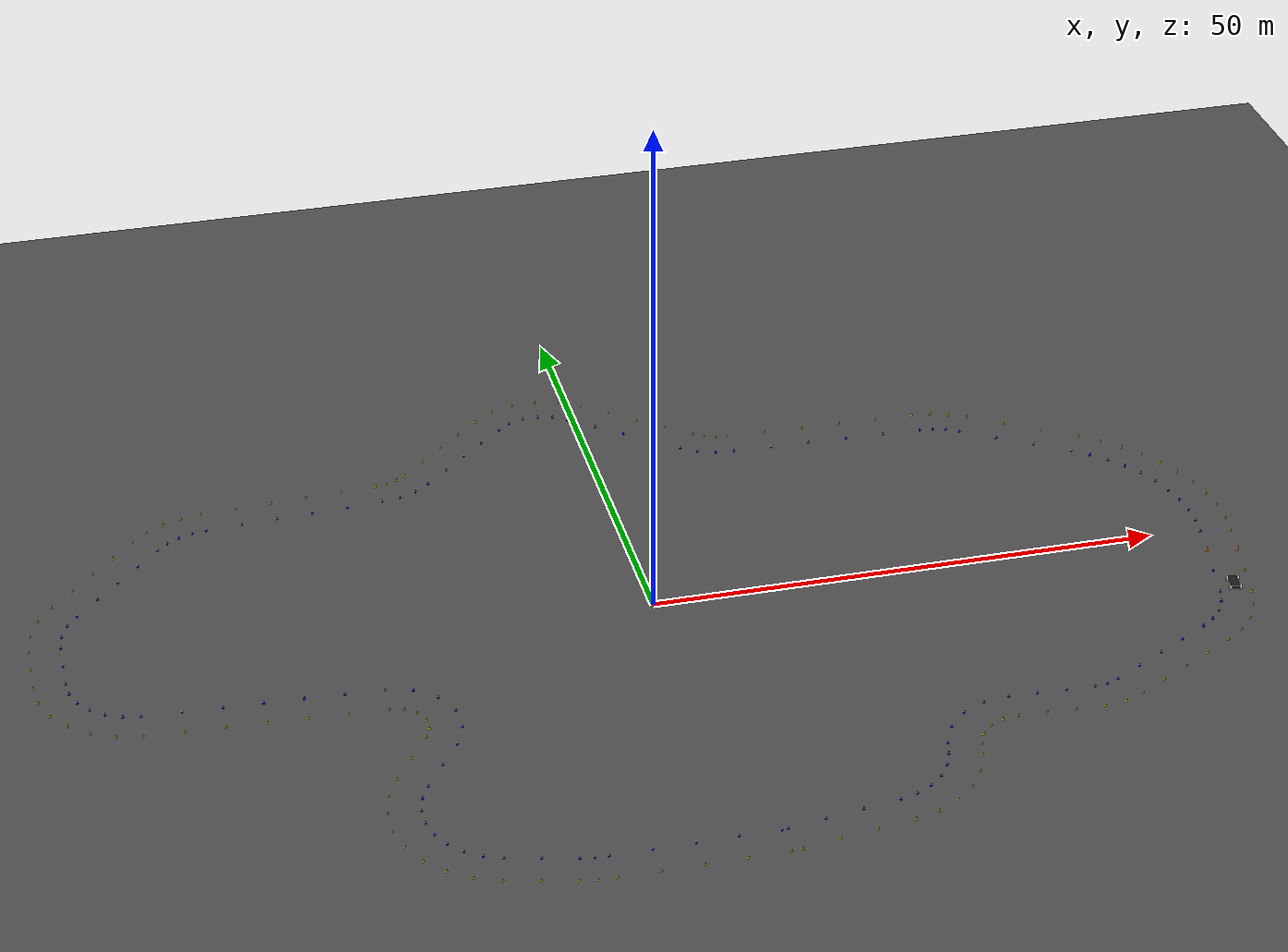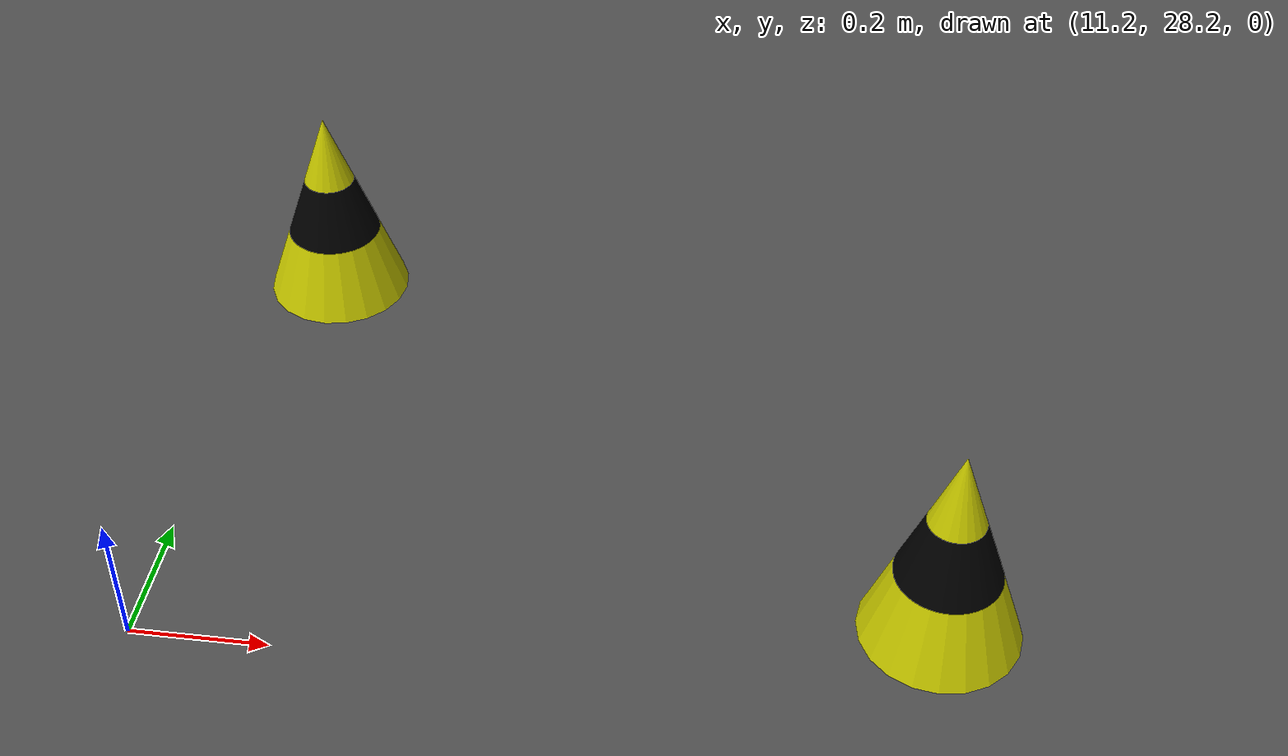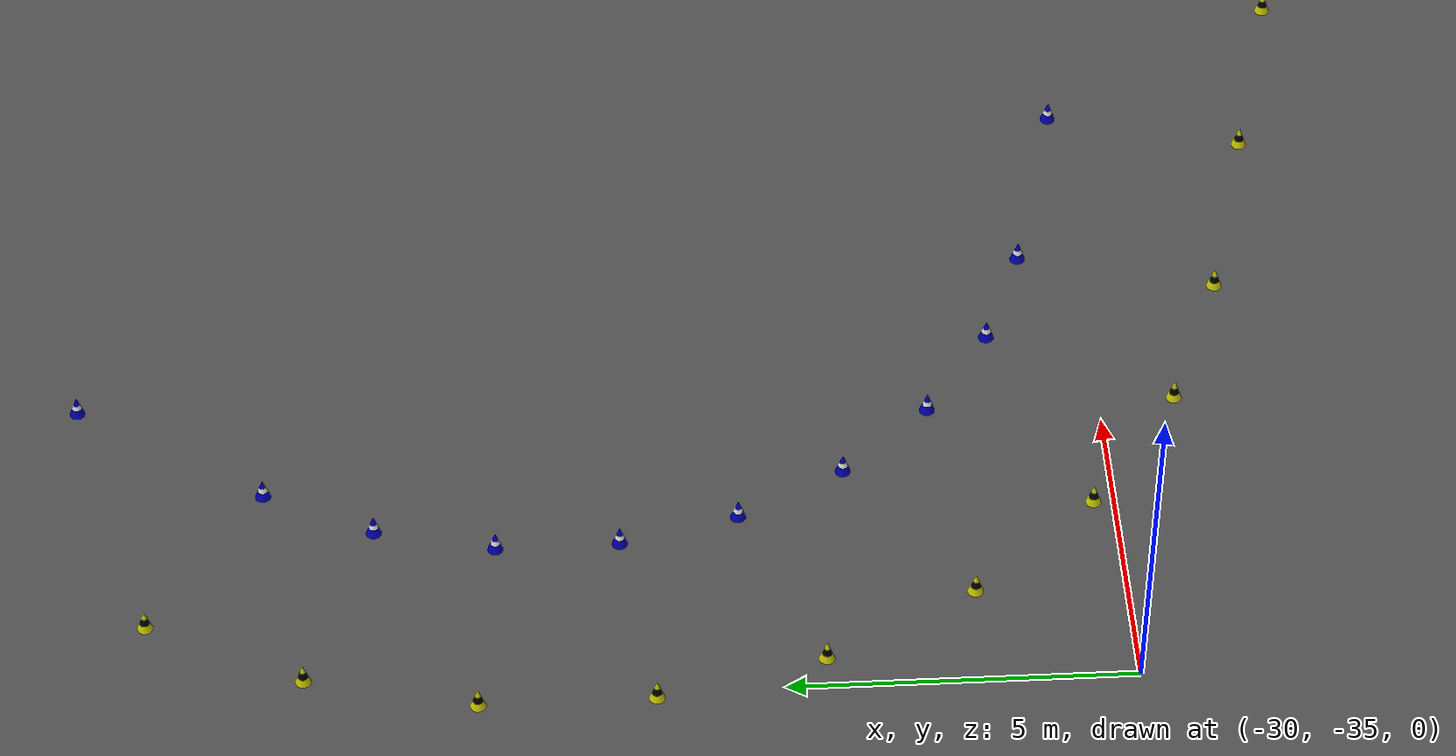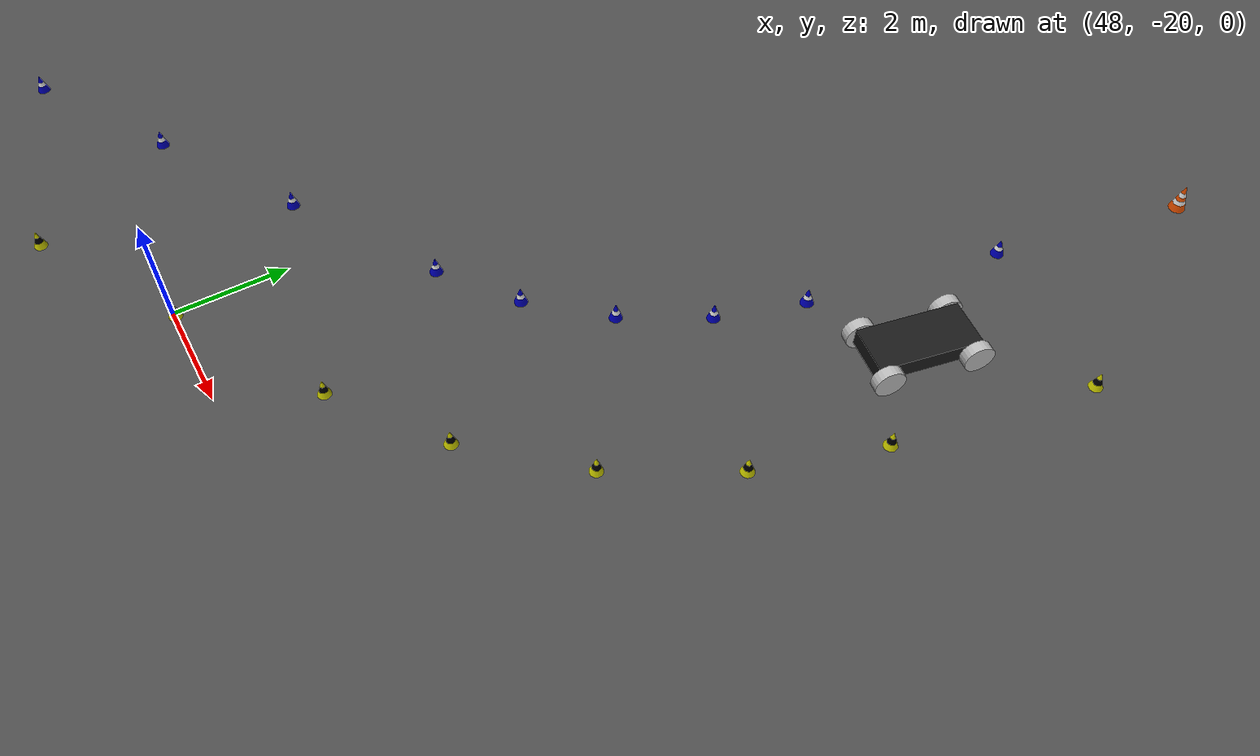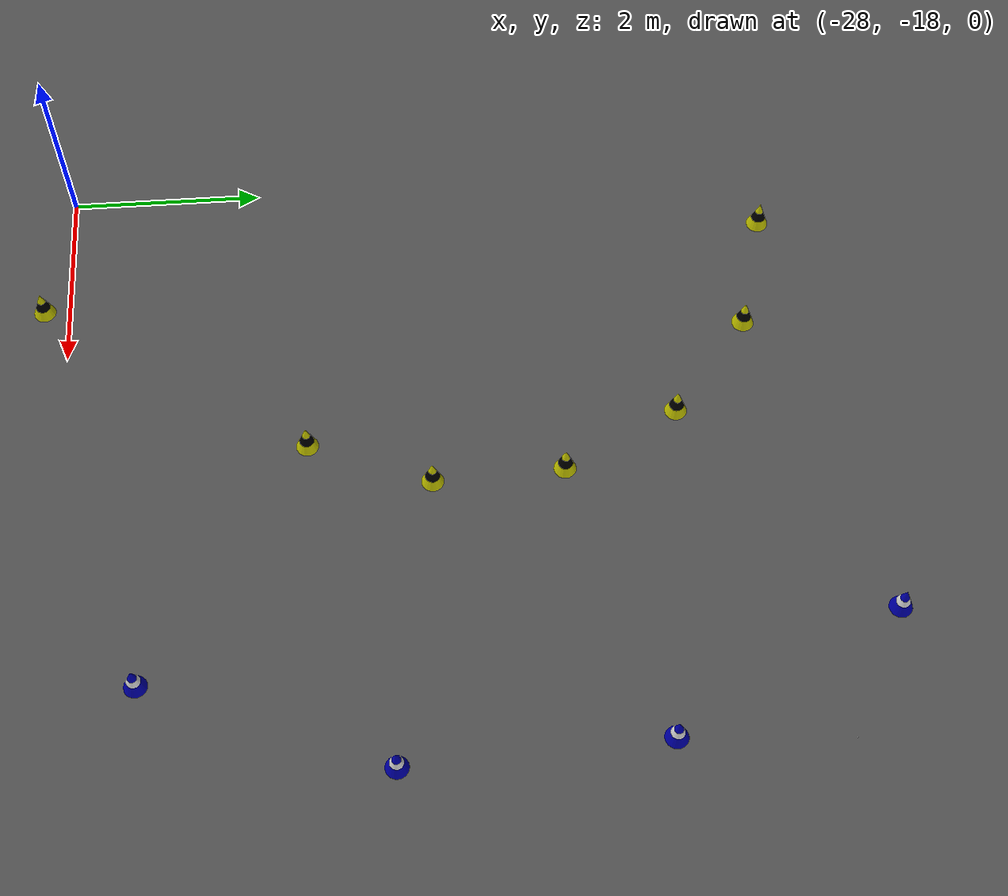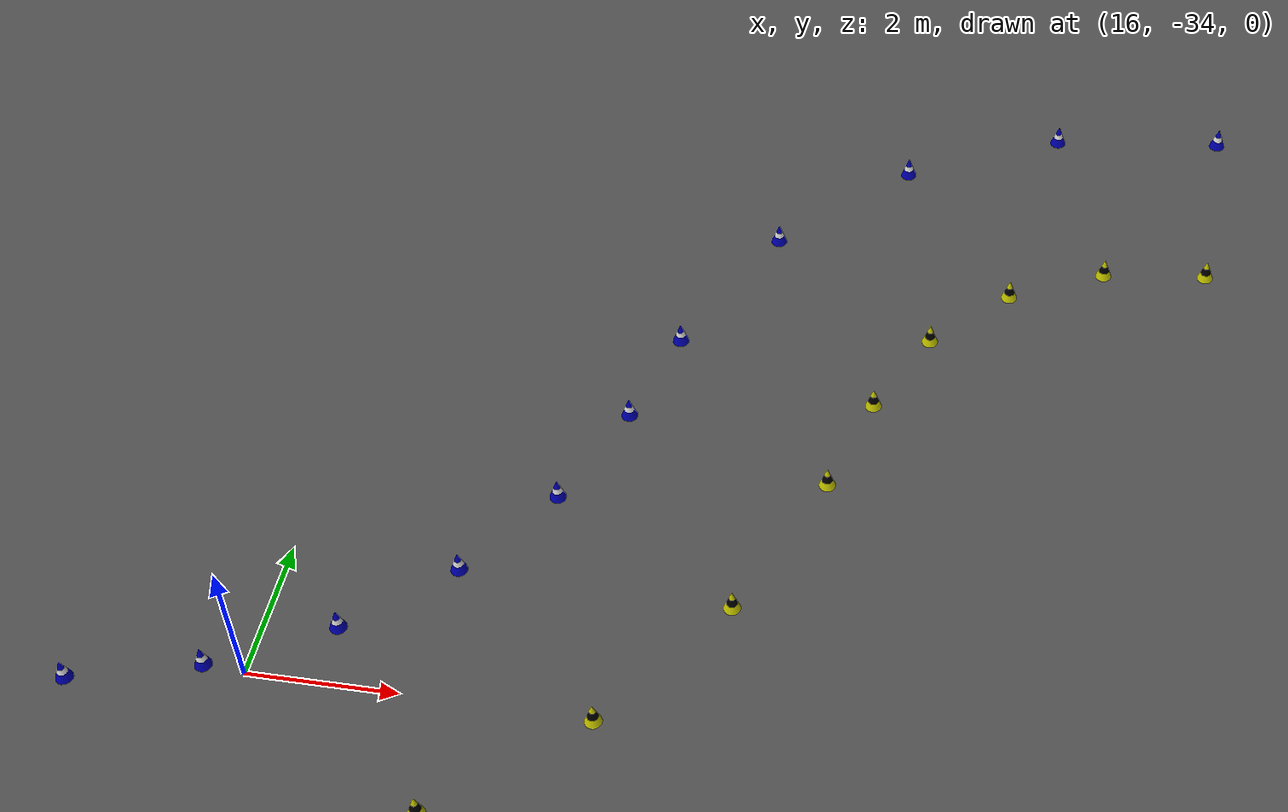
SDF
<?xml version="1.0" ?>
<sdf version="1.11">
  <world name="trackdrive">

    <physics name="default" type="dart">
      <max_step_size>0.001</max_step_size>
      <real_time_factor>1.0</real_time_factor>
    </physics>

    <!-- Required Gazebo system plugins -->
    <plugin filename="gz-sim-physics-system"
            name="gz::sim::systems::Physics"/>
    <plugin filename="gz-sim-scene-broadcaster-system"
            name="gz::sim::systems::SceneBroadcaster"/>
    <plugin filename="gz-sim-user-commands-system"
            name="gz::sim::systems::UserCommands"/>
    <!-- Required for camera/lidar sensors to actually initialize and publish
         data — without this, sensor elements in a model are inert. -->
    <plugin filename="gz-sim-sensors-system"
            name="gz::sim::systems::Sensors">
      <render_engine>ogre2</render_engine>
    </plugin>
    <plugin filename="gz-sim-imu-system"
            name="gz::sim::systems::Imu"/>
    <plugin filename="gz-sim-navsat-system"
            name="gz::sim::systems::NavSat"/>

    <spherical_coordinates>
      <surface_model>EARTH_WGS84</surface_model>
      <world_frame_orientation>ENU</world_frame_orientation>
      <latitude_deg>32.9</latitude_deg>
      <longitude_deg>-117.1</longitude_deg>
      <elevation>100</elevation>
      <heading_deg>0</heading_deg>
    </spherical_coordinates>

    <!-- Lighting -->
    <light name="sun" type="directional">
      <cast_shadows>true</cast_shadows>
      <pose>0 0 10 0 0 0</pose>
      <diffuse>1 1 1 1</diffuse>
      <specular>0.4 0.4 0.4 1</specular>
      <direction>-0.5 0.1 -0.9</direction>
    </light>

    <!-- Ground plane -->
    <model name="ground_plane">
      <static>true</static>
      <link name="link">
        <collision name="collision">
          <geometry>
            <plane>
              <normal>0 0 1</normal>
              <size>300 300</size>
            </plane>
          </geometry>
        </collision>
        <visual name="visual">
          <geometry>
            <plane>
              <normal>0 0 1</normal>
              <size>300 300</size>
            </plane>
          </geometry>
          <material>
            <ambient>0.3 0.3 0.3 1</ambient>
            <diffuse>0.3 0.3 0.3 1</diffuse>
          </material>
        </visual>
      </link>
    </model>

    <include>
      <uri>model://fsd_car</uri>
      <pose>54.697 -9.961 0.31 0 0 1.3748</pose>
    </include>

    <!-- ==================== ORANGE — start/finish gate ==================== -->
    <include>
      <uri>model://cone_orange</uri>
      <name>cone_orange_00</name>
      <pose>54.394 -3.784 0.2525 0 0 0</pose>
    </include>
    <include>
      <uri>model://cone_orange</uri>
      <name>cone_orange_01</name>
      <pose>57.337 -4.368 0.2525 0 0 0</pose>
    </include>

    <!-- ==================== BOUNDARY — blue (left) / yellow (right) ==================== -->
    <include>
      <uri>model://cone_blue</uri>
      <name>cone_blue_000</name>
      <pose>55.053 -0.458 0.1625 0 0 0</pose>
    </include>
    <include>
      <uri>model://cone_yellow</uri>
      <name>cone_yellow_000</name>
      <pose>57.996 -1.042 0.1625 0 0 0</pose>
    </include>
    <include>
      <uri>model://cone_blue</uri>
      <name>cone_blue_001</name>
      <pose>55.322 1.489 0.1625 0 0 0</pose>
    </include>
    <include>
      <uri>model://cone_yellow</uri>
      <name>cone_yellow_001</name>
      <pose>58.312 1.259 0.1625 0 0 0</pose>
    </include>
    <include>
      <uri>model://cone_blue</uri>
      <name>cone_blue_002</name>
      <pose>55.356 3.455 0.1625 0 0 0</pose>
    </include>
    <include>
      <uri>model://cone_yellow</uri>
      <name>cone_yellow_002</name>
      <pose>58.353 3.582 0.1625 0 0 0</pose>
    </include>
    <include>
      <uri>model://cone_blue</uri>
      <name>cone_blue_003</name>
      <pose>55.156 5.410 0.1625 0 0 0</pose>
    </include>
    <include>
      <uri>model://cone_yellow</uri>
      <name>cone_yellow_003</name>
      <pose>58.115 5.893 0.1625 0 0 0</pose>
    </include>
    <include>
      <uri>model://cone_blue</uri>
      <name>cone_blue_004</name>
      <pose>54.724 7.328 0.1625 0 0 0</pose>
    </include>
    <include>
      <uri>model://cone_yellow</uri>
      <name>cone_yellow_004</name>
      <pose>57.606 8.159 0.1625 0 0 0</pose>
    </include>
    <include>
      <uri>model://cone_blue</uri>
      <name>cone_blue_005</name>
      <pose>54.067 9.180 0.1625 0 0 0</pose>
    </include>
    <include>
      <uri>model://cone_yellow</uri>
      <name>cone_yellow_005</name>
      <pose>56.831 10.349 0.1625 0 0 0</pose>
    </include>
    <include>
      <uri>model://cone_blue</uri>
      <name>cone_blue_006</name>
      <pose>53.195 10.942 0.1625 0 0 0</pose>
    </include>
    <include>
      <uri>model://cone_yellow</uri>
      <name>cone_yellow_006</name>
      <pose>55.800 12.430 0.1625 0 0 0</pose>
    </include>
    <include>
      <uri>model://cone_blue</uri>
      <name>cone_blue_007</name>
      <pose>52.121 12.587 0.1625 0 0 0</pose>
    </include>
    <include>
      <uri>model://cone_yellow</uri>
      <name>cone_yellow_007</name>
      <pose>54.529 14.375 0.1625 0 0 0</pose>
    </include>
    <include>
      <uri>model://cone_blue</uri>
      <name>cone_blue_008</name>
      <pose>50.858 14.093 0.1625 0 0 0</pose>
    </include>
    <include>
      <uri>model://cone_yellow</uri>
      <name>cone_yellow_008</name>
      <pose>53.038 16.155 0.1625 0 0 0</pose>
    </include>
    <include>
      <uri>model://cone_blue</uri>
      <name>cone_blue_009</name>
      <pose>49.424 15.438 0.1625 0 0 0</pose>
    </include>
    <include>
      <uri>model://cone_yellow</uri>
      <name>cone_yellow_009</name>
      <pose>51.344 17.744 0.1625 0 0 0</pose>
    </include>
    <include>
      <uri>model://cone_blue</uri>
      <name>cone_blue_010</name>
      <pose>47.841 16.603 0.1625 0 0 0</pose>
    </include>
    <include>
      <uri>model://cone_yellow</uri>
      <name>cone_yellow_010</name>
      <pose>49.472 19.121 0.1625 0 0 0</pose>
    </include>
    <include>
      <uri>model://cone_blue</uri>
      <name>cone_blue_011</name>
      <pose>44.550 18.735 0.1625 0 0 0</pose>
    </include>
    <include>
      <uri>model://cone_yellow</uri>
      <name>cone_yellow_011</name>
      <pose>46.181 21.253 0.1625 0 0 0</pose>
    </include>
    <include>
      <uri>model://cone_blue</uri>
      <name>cone_blue_012</name>
      <pose>41.260 20.867 0.1625 0 0 0</pose>
    </include>
    <include>
      <uri>model://cone_yellow</uri>
      <name>cone_yellow_012</name>
      <pose>42.891 23.385 0.1625 0 0 0</pose>
    </include>
    <include>
      <uri>model://cone_blue</uri>
      <name>cone_blue_013</name>
      <pose>37.969 22.999 0.1625 0 0 0</pose>
    </include>
    <include>
      <uri>model://cone_yellow</uri>
      <name>cone_yellow_013</name>
      <pose>39.600 25.517 0.1625 0 0 0</pose>
    </include>
    <include>
      <uri>model://cone_blue</uri>
      <name>cone_blue_014</name>
      <pose>36.763 23.633 0.1625 0 0 0</pose>
    </include>
    <include>
      <uri>model://cone_yellow</uri>
      <name>cone_yellow_014</name>
      <pose>37.912 26.404 0.1625 0 0 0</pose>
    </include>
    <include>
      <uri>model://cone_blue</uri>
      <name>cone_blue_015</name>
      <pose>35.462 24.038 0.1625 0 0 0</pose>
    </include>
    <include>
      <uri>model://cone_yellow</uri>
      <name>cone_yellow_015</name>
      <pose>36.090 26.972 0.1625 0 0 0</pose>
    </include>
    <include>
      <uri>model://cone_blue</uri>
      <name>cone_blue_016</name>
      <pose>34.109 24.201 0.1625 0 0 0</pose>
    </include>
    <include>
      <uri>model://cone_yellow</uri>
      <name>cone_yellow_016</name>
      <pose>34.195 27.200 0.1625 0 0 0</pose>
    </include>
    <include>
      <uri>model://cone_blue</uri>
      <name>cone_blue_017</name>
      <pose>30.195 24.315 0.1625 0 0 0</pose>
    </include>
    <include>
      <uri>model://cone_yellow</uri>
      <name>cone_yellow_017</name>
      <pose>30.281 27.313 0.1625 0 0 0</pose>
    </include>
    <include>
      <uri>model://cone_blue</uri>
      <name>cone_blue_018</name>
      <pose>26.281 24.428 0.1625 0 0 0</pose>
    </include>
    <include>
      <uri>model://cone_yellow</uri>
      <name>cone_yellow_018</name>
      <pose>26.367 27.427 0.1625 0 0 0</pose>
    </include>
    <include>
      <uri>model://cone_blue</uri>
      <name>cone_blue_019</name>
      <pose>22.365 24.541 0.1625 0 0 0</pose>
    </include>
    <include>
      <uri>model://cone_yellow</uri>
      <name>cone_yellow_019</name>
      <pose>22.453 27.540 0.1625 0 0 0</pose>
    </include>
    <include>
      <uri>model://cone_blue</uri>
      <name>cone_blue_020</name>
      <pose>18.451 24.654 0.1625 0 0 0</pose>
    </include>
    <include>
      <uri>model://cone_yellow</uri>
      <name>cone_yellow_020</name>
      <pose>18.538 27.653 0.1625 0 0 0</pose>
    </include>
    <include>
      <uri>model://cone_blue</uri>
      <name>cone_blue_021</name>
      <pose>14.538 24.768 0.1625 0 0 0</pose>
    </include>
    <include>
      <uri>model://cone_yellow</uri>
      <name>cone_yellow_021</name>
      <pose>14.624 27.766 0.1625 0 0 0</pose>
    </include>
    <include>
      <uri>model://cone_blue</uri>
      <name>cone_blue_022</name>
      <pose>12.700 25.023 0.1625 0 0 0</pose>
    </include>
    <include>
      <uri>model://cone_yellow</uri>
      <name>cone_yellow_022</name>
      <pose>13.436 27.932 0.1625 0 0 0</pose>
    </include>
    <include>
      <uri>model://cone_blue</uri>
      <name>cone_blue_023</name>
      <pose>10.960 25.672 0.1625 0 0 0</pose>
    </include>
    <include>
      <uri>model://cone_yellow</uri>
      <name>cone_yellow_023</name>
      <pose>12.311 28.352 0.1625 0 0 0</pose>
    </include>
    <include>
      <uri>model://cone_blue</uri>
      <name>cone_blue_024</name>
      <pose>9.404 26.683 0.1625 0 0 0</pose>
    </include>
    <include>
      <uri>model://cone_yellow</uri>
      <name>cone_yellow_024</name>
      <pose>11.302 29.005 0.1625 0 0 0</pose>
    </include>
    <include>
      <uri>model://cone_blue</uri>
      <name>cone_blue_025</name>
      <pose>6.915 28.717 0.1625 0 0 0</pose>
    </include>
    <include>
      <uri>model://cone_yellow</uri>
      <name>cone_yellow_025</name>
      <pose>8.814 31.040 0.1625 0 0 0</pose>
    </include>
    <include>
      <uri>model://cone_blue</uri>
      <name>cone_blue_026</name>
      <pose>4.425 30.752 0.1625 0 0 0</pose>
    </include>
    <include>
      <uri>model://cone_yellow</uri>
      <name>cone_yellow_026</name>
      <pose>6.323 33.075 0.1625 0 0 0</pose>
    </include>
    <include>
      <uri>model://cone_blue</uri>
      <name>cone_blue_027</name>
      <pose>1.936 32.787 0.1625 0 0 0</pose>
    </include>
    <include>
      <uri>model://cone_yellow</uri>
      <name>cone_yellow_027</name>
      <pose>3.835 35.110 0.1625 0 0 0</pose>
    </include>
    <include>
      <uri>model://cone_blue</uri>
      <name>cone_blue_028</name>
      <pose>-0.553 34.822 0.1625 0 0 0</pose>
    </include>
    <include>
      <uri>model://cone_yellow</uri>
      <name>cone_yellow_028</name>
      <pose>1.346 37.144 0.1625 0 0 0</pose>
    </include>
    <include>
      <uri>model://cone_blue</uri>
      <name>cone_blue_029</name>
      <pose>-1.908 35.636 0.1625 0 0 0</pose>
    </include>
    <include>
      <uri>model://cone_yellow</uri>
      <name>cone_yellow_029</name>
      <pose>-0.748 38.402 0.1625 0 0 0</pose>
    </include>
    <include>
      <uri>model://cone_blue</uri>
      <name>cone_blue_030</name>
      <pose>-3.438 36.031 0.1625 0 0 0</pose>
    </include>
    <include>
      <uri>model://cone_yellow</uri>
      <name>cone_yellow_030</name>
      <pose>-3.113 39.013 0.1625 0 0 0</pose>
    </include>
    <include>
      <uri>model://cone_blue</uri>
      <name>cone_blue_031</name>
      <pose>-5.017 35.974 0.1625 0 0 0</pose>
    </include>
    <include>
      <uri>model://cone_yellow</uri>
      <name>cone_yellow_031</name>
      <pose>-5.554 38.926 0.1625 0 0 0</pose>
    </include>
    <include>
      <uri>model://cone_blue</uri>
      <name>cone_blue_032</name>
      <pose>-6.515 35.471 0.1625 0 0 0</pose>
    </include>
    <include>
      <uri>model://cone_yellow</uri>
      <name>cone_yellow_032</name>
      <pose>-7.869 38.149 0.1625 0 0 0</pose>
    </include>
    <include>
      <uri>model://cone_blue</uri>
      <name>cone_blue_033</name>
      <pose>-7.809 34.563 0.1625 0 0 0</pose>
    </include>
    <include>
      <uri>model://cone_yellow</uri>
      <name>cone_yellow_033</name>
      <pose>-9.868 36.745 0.1625 0 0 0</pose>
    </include>
    <include>
      <uri>model://cone_blue</uri>
      <name>cone_blue_034</name>
      <pose>-10.049 32.448 0.1625 0 0 0</pose>
    </include>
    <include>
      <uri>model://cone_yellow</uri>
      <name>cone_yellow_034</name>
      <pose>-12.108 34.630 0.1625 0 0 0</pose>
    </include>
    <include>
      <uri>model://cone_blue</uri>
      <name>cone_blue_035</name>
      <pose>-12.291 30.334 0.1625 0 0 0</pose>
    </include>
    <include>
      <uri>model://cone_yellow</uri>
      <name>cone_yellow_035</name>
      <pose>-14.349 32.515 0.1625 0 0 0</pose>
    </include>
    <include>
      <uri>model://cone_blue</uri>
      <name>cone_blue_036</name>
      <pose>-14.532 28.219 0.1625 0 0 0</pose>
    </include>
    <include>
      <uri>model://cone_yellow</uri>
      <name>cone_yellow_036</name>
      <pose>-16.590 30.401 0.1625 0 0 0</pose>
    </include>
    <include>
      <uri>model://cone_blue</uri>
      <name>cone_blue_037</name>
      <pose>-16.771 26.104 0.1625 0 0 0</pose>
    </include>
    <include>
      <uri>model://cone_yellow</uri>
      <name>cone_yellow_037</name>
      <pose>-18.831 28.286 0.1625 0 0 0</pose>
    </include>
    <include>
      <uri>model://cone_blue</uri>
      <name>cone_blue_038</name>
      <pose>-18.261 24.995 0.1625 0 0 0</pose>
    </include>
    <include>
      <uri>model://cone_yellow</uri>
      <name>cone_yellow_038</name>
      <pose>-19.761 27.593 0.1625 0 0 0</pose>
    </include>
    <include>
      <uri>model://cone_blue</uri>
      <name>cone_blue_039</name>
      <pose>-19.965 24.259 0.1625 0 0 0</pose>
    </include>
    <include>
      <uri>model://cone_yellow</uri>
      <name>cone_yellow_039</name>
      <pose>-20.828 27.133 0.1625 0 0 0</pose>
    </include>
    <include>
      <uri>model://cone_blue</uri>
      <name>cone_blue_040</name>
      <pose>-21.794 23.936 0.1625 0 0 0</pose>
    </include>
    <include>
      <uri>model://cone_yellow</uri>
      <name>cone_yellow_040</name>
      <pose>-21.971 26.931 0.1625 0 0 0</pose>
    </include>
    <include>
      <uri>model://cone_blue</uri>
      <name>cone_blue_041</name>
      <pose>-25.323 23.729 0.1625 0 0 0</pose>
    </include>
    <include>
      <uri>model://cone_yellow</uri>
      <name>cone_yellow_041</name>
      <pose>-25.499 26.724 0.1625 0 0 0</pose>
    </include>
    <include>
      <uri>model://cone_blue</uri>
      <name>cone_blue_042</name>
      <pose>-28.853 23.522 0.1625 0 0 0</pose>
    </include>
    <include>
      <uri>model://cone_yellow</uri>
      <name>cone_yellow_042</name>
      <pose>-29.029 26.517 0.1625 0 0 0</pose>
    </include>
    <include>
      <uri>model://cone_blue</uri>
      <name>cone_blue_043</name>
      <pose>-32.382 23.315 0.1625 0 0 0</pose>
    </include>
    <include>
      <uri>model://cone_yellow</uri>
      <name>cone_yellow_043</name>
      <pose>-32.558 26.310 0.1625 0 0 0</pose>
    </include>
    <include>
      <uri>model://cone_blue</uri>
      <name>cone_blue_044</name>
      <pose>-35.912 23.108 0.1625 0 0 0</pose>
    </include>
    <include>
      <uri>model://cone_yellow</uri>
      <name>cone_yellow_044</name>
      <pose>-36.087 26.103 0.1625 0 0 0</pose>
    </include>
    <include>
      <uri>model://cone_blue</uri>
      <name>cone_blue_045</name>
      <pose>-39.441 22.901 0.1625 0 0 0</pose>
    </include>
    <include>
      <uri>model://cone_yellow</uri>
      <name>cone_yellow_045</name>
      <pose>-39.617 25.896 0.1625 0 0 0</pose>
    </include>
    <include>
      <uri>model://cone_blue</uri>
      <name>cone_blue_046</name>
      <pose>-40.859 22.681 0.1625 0 0 0</pose>
    </include>
    <include>
      <uri>model://cone_yellow</uri>
      <name>cone_yellow_046</name>
      <pose>-41.602 25.587 0.1625 0 0 0</pose>
    </include>
    <include>
      <uri>model://cone_blue</uri>
      <name>cone_blue_047</name>
      <pose>-42.209 22.194 0.1625 0 0 0</pose>
    </include>
    <include>
      <uri>model://cone_yellow</uri>
      <name>cone_yellow_047</name>
      <pose>-43.492 24.906 0.1625 0 0 0</pose>
    </include>
    <include>
      <uri>model://cone_blue</uri>
      <name>cone_blue_048</name>
      <pose>-43.441 21.459 0.1625 0 0 0</pose>
    </include>
    <include>
      <uri>model://cone_yellow</uri>
      <name>cone_yellow_048</name>
      <pose>-45.218 23.877 0.1625 0 0 0</pose>
    </include>
    <include>
      <uri>model://cone_blue</uri>
      <name>cone_blue_049</name>
      <pose>-44.511 20.503 0.1625 0 0 0</pose>
    </include>
    <include>
      <uri>model://cone_yellow</uri>
      <name>cone_yellow_049</name>
      <pose>-46.715 22.539 0.1625 0 0 0</pose>
    </include>
    <include>
      <uri>model://cone_blue</uri>
      <name>cone_blue_050</name>
      <pose>-46.691 18.144 0.1625 0 0 0</pose>
    </include>
    <include>
      <uri>model://cone_yellow</uri>
      <name>cone_yellow_050</name>
      <pose>-48.895 20.179 0.1625 0 0 0</pose>
    </include>
    <include>
      <uri>model://cone_blue</uri>
      <name>cone_blue_051</name>
      <pose>-48.871 15.784 0.1625 0 0 0</pose>
    </include>
    <include>
      <uri>model://cone_yellow</uri>
      <name>cone_yellow_051</name>
      <pose>-51.075 17.819 0.1625 0 0 0</pose>
    </include>
    <include>
      <uri>model://cone_blue</uri>
      <name>cone_blue_052</name>
      <pose>-51.051 13.424 0.1625 0 0 0</pose>
    </include>
    <include>
      <uri>model://cone_yellow</uri>
      <name>cone_yellow_052</name>
      <pose>-53.255 15.460 0.1625 0 0 0</pose>
    </include>
    <include>
      <uri>model://cone_blue</uri>
      <name>cone_blue_053</name>
      <pose>-53.230 11.065 0.1625 0 0 0</pose>
    </include>
    <include>
      <uri>model://cone_yellow</uri>
      <name>cone_yellow_053</name>
      <pose>-55.434 13.100 0.1625 0 0 0</pose>
    </include>
    <include>
      <uri>model://cone_blue</uri>
      <name>cone_blue_054</name>
      <pose>-54.286 9.603 0.1625 0 0 0</pose>
    </include>
    <include>
      <uri>model://cone_yellow</uri>
      <name>cone_yellow_054</name>
      <pose>-56.912 11.054 0.1625 0 0 0</pose>
    </include>
    <include>
      <uri>model://cone_blue</uri>
      <name>cone_blue_055</name>
      <pose>-54.962 7.931 0.1625 0 0 0</pose>
    </include>
    <include>
      <uri>model://cone_yellow</uri>
      <name>cone_yellow_055</name>
      <pose>-57.858 8.713 0.1625 0 0 0</pose>
    </include>
    <include>
      <uri>model://cone_blue</uri>
      <name>cone_blue_056</name>
      <pose>-55.219 6.147 0.1625 0 0 0</pose>
    </include>
    <include>
      <uri>model://cone_yellow</uri>
      <name>cone_yellow_056</name>
      <pose>-58.218 6.215 0.1625 0 0 0</pose>
    </include>
    <include>
      <uri>model://cone_blue</uri>
      <name>cone_blue_057</name>
      <pose>-55.286 3.223 0.1625 0 0 0</pose>
    </include>
    <include>
      <uri>model://cone_yellow</uri>
      <name>cone_yellow_057</name>
      <pose>-58.285 3.292 0.1625 0 0 0</pose>
    </include>
    <include>
      <uri>model://cone_blue</uri>
      <name>cone_blue_058</name>
      <pose>-55.353 0.300 0.1625 0 0 0</pose>
    </include>
    <include>
      <uri>model://cone_yellow</uri>
      <name>cone_yellow_058</name>
      <pose>-58.352 0.369 0.1625 0 0 0</pose>
    </include>
    <include>
      <uri>model://cone_blue</uri>
      <name>cone_blue_059</name>
      <pose>-55.178 -1.353 0.1625 0 0 0</pose>
    </include>
    <include>
      <uri>model://cone_yellow</uri>
      <name>cone_yellow_059</name>
      <pose>-58.097 -2.047 0.1625 0 0 0</pose>
    </include>
    <include>
      <uri>model://cone_blue</uri>
      <name>cone_blue_060</name>
      <pose>-54.590 -2.907 0.1625 0 0 0</pose>
    </include>
    <include>
      <uri>model://cone_yellow</uri>
      <name>cone_yellow_060</name>
      <pose>-57.237 -4.319 0.1625 0 0 0</pose>
    </include>
    <include>
      <uri>model://cone_blue</uri>
      <name>cone_blue_061</name>
      <pose>-53.627 -4.262 0.1625 0 0 0</pose>
    </include>
    <include>
      <uri>model://cone_yellow</uri>
      <name>cone_yellow_061</name>
      <pose>-55.828 -6.299 0.1625 0 0 0</pose>
    </include>
    <include>
      <uri>model://cone_blue</uri>
      <name>cone_blue_062</name>
      <pose>-52.352 -5.328 0.1625 0 0 0</pose>
    </include>
    <include>
      <uri>model://cone_yellow</uri>
      <name>cone_yellow_062</name>
      <pose>-53.965 -7.857 0.1625 0 0 0</pose>
    </include>
    <include>
      <uri>model://cone_blue</uri>
      <name>cone_blue_063</name>
      <pose>-50.847 -6.035 0.1625 0 0 0</pose>
    </include>
    <include>
      <uri>model://cone_yellow</uri>
      <name>cone_yellow_063</name>
      <pose>-51.767 -8.891 0.1625 0 0 0</pose>
    </include>
    <include>
      <uri>model://cone_blue</uri>
      <name>cone_blue_064</name>
      <pose>-49.212 -6.338 0.1625 0 0 0</pose>
    </include>
    <include>
      <uri>model://cone_yellow</uri>
      <name>cone_yellow_064</name>
      <pose>-49.377 -9.334 0.1625 0 0 0</pose>
    </include>
    <include>
      <uri>model://cone_blue</uri>
      <name>cone_blue_065</name>
      <pose>-45.526 -6.541 0.1625 0 0 0</pose>
    </include>
    <include>
      <uri>model://cone_yellow</uri>
      <name>cone_yellow_065</name>
      <pose>-45.691 -9.537 0.1625 0 0 0</pose>
    </include>
    <include>
      <uri>model://cone_blue</uri>
      <name>cone_blue_066</name>
      <pose>-41.841 -6.745 0.1625 0 0 0</pose>
    </include>
    <include>
      <uri>model://cone_yellow</uri>
      <name>cone_yellow_066</name>
      <pose>-42.007 -9.740 0.1625 0 0 0</pose>
    </include>
    <include>
      <uri>model://cone_blue</uri>
      <name>cone_blue_067</name>
      <pose>-38.155 -6.948 0.1625 0 0 0</pose>
    </include>
    <include>
      <uri>model://cone_yellow</uri>
      <name>cone_yellow_067</name>
      <pose>-38.320 -9.943 0.1625 0 0 0</pose>
    </include>
    <include>
      <uri>model://cone_blue</uri>
      <name>cone_blue_068</name>
      <pose>-34.469 -7.151 0.1625 0 0 0</pose>
    </include>
    <include>
      <uri>model://cone_yellow</uri>
      <name>cone_yellow_068</name>
      <pose>-34.635 -10.146 0.1625 0 0 0</pose>
    </include>
    <include>
      <uri>model://cone_blue</uri>
      <name>cone_blue_069</name>
      <pose>-30.783 -7.354 0.1625 0 0 0</pose>
    </include>
    <include>
      <uri>model://cone_yellow</uri>
      <name>cone_yellow_069</name>
      <pose>-30.948 -10.349 0.1625 0 0 0</pose>
    </include>
    <include>
      <uri>model://cone_blue</uri>
      <name>cone_blue_070</name>
      <pose>-27.097 -7.557 0.1625 0 0 0</pose>
    </include>
    <include>
      <uri>model://cone_yellow</uri>
      <name>cone_yellow_070</name>
      <pose>-27.264 -10.552 0.1625 0 0 0</pose>
    </include>
    <include>
      <uri>model://cone_blue</uri>
      <name>cone_blue_071</name>
      <pose>-24.599 -8.236 0.1625 0 0 0</pose>
    </include>
    <include>
      <uri>model://cone_yellow</uri>
      <name>cone_yellow_071</name>
      <pose>-25.974 -10.903 0.1625 0 0 0</pose>
    </include>
    <include>
      <uri>model://cone_blue</uri>
      <name>cone_blue_072</name>
      <pose>-22.596 -9.877 0.1625 0 0 0</pose>
    </include>
    <include>
      <uri>model://cone_yellow</uri>
      <name>cone_yellow_072</name>
      <pose>-24.939 -11.750 0.1625 0 0 0</pose>
    </include>
    <include>
      <uri>model://cone_blue</uri>
      <name>cone_blue_073</name>
      <pose>-21.436 -12.194 0.1625 0 0 0</pose>
    </include>
    <include>
      <uri>model://cone_yellow</uri>
      <name>cone_yellow_073</name>
      <pose>-24.341 -12.946 0.1625 0 0 0</pose>
    </include>
    <include>
      <uri>model://cone_blue</uri>
      <name>cone_blue_074</name>
      <pose>-21.325 -14.781 0.1625 0 0 0</pose>
    </include>
    <include>
      <uri>model://cone_yellow</uri>
      <name>cone_yellow_074</name>
      <pose>-24.283 -14.281 0.1625 0 0 0</pose>
    </include>
    <include>
      <uri>model://cone_blue</uri>
      <name>cone_blue_075</name>
      <pose>-22.282 -17.188 0.1625 0 0 0</pose>
    </include>
    <include>
      <uri>model://cone_yellow</uri>
      <name>cone_yellow_075</name>
      <pose>-24.777 -15.523 0.1625 0 0 0</pose>
    </include>
    <include>
      <uri>model://cone_blue</uri>
      <name>cone_blue_076</name>
      <pose>-24.109 -19.928 0.1625 0 0 0</pose>
    </include>
    <include>
      <uri>model://cone_yellow</uri>
      <name>cone_yellow_076</name>
      <pose>-26.605 -18.263 0.1625 0 0 0</pose>
    </include>
    <include>
      <uri>model://cone_blue</uri>
      <name>cone_blue_077</name>
      <pose>-25.936 -22.667 0.1625 0 0 0</pose>
    </include>
    <include>
      <uri>model://cone_yellow</uri>
      <name>cone_yellow_077</name>
      <pose>-28.432 -21.002 0.1625 0 0 0</pose>
    </include>
    <include>
      <uri>model://cone_blue</uri>
      <name>cone_blue_078</name>
      <pose>-26.745 -24.265 0.1625 0 0 0</pose>
    </include>
    <include>
      <uri>model://cone_yellow</uri>
      <name>cone_yellow_078</name>
      <pose>-29.564 -23.239 0.1625 0 0 0</pose>
    </include>
    <include>
      <uri>model://cone_blue</uri>
      <name>cone_blue_079</name>
      <pose>-27.152 -26.008 0.1625 0 0 0</pose>
    </include>
    <include>
      <uri>model://cone_yellow</uri>
      <name>cone_yellow_079</name>
      <pose>-30.134 -25.680 0.1625 0 0 0</pose>
    </include>
    <include>
      <uri>model://cone_blue</uri>
      <name>cone_blue_080</name>
      <pose>-27.134 -27.799 0.1625 0 0 0</pose>
    </include>
    <include>
      <uri>model://cone_yellow</uri>
      <name>cone_yellow_080</name>
      <pose>-30.109 -28.187 0.1625 0 0 0</pose>
    </include>
    <include>
      <uri>model://cone_blue</uri>
      <name>cone_blue_081</name>
      <pose>-26.692 -29.534 0.1625 0 0 0</pose>
    </include>
    <include>
      <uri>model://cone_yellow</uri>
      <name>cone_yellow_081</name>
      <pose>-29.491 -30.616 0.1625 0 0 0</pose>
    </include>
    <include>
      <uri>model://cone_blue</uri>
      <name>cone_blue_082</name>
      <pose>-25.852 -31.115 0.1625 0 0 0</pose>
    </include>
    <include>
      <uri>model://cone_yellow</uri>
      <name>cone_yellow_082</name>
      <pose>-28.314 -32.829 0.1625 0 0 0</pose>
    </include>
    <include>
      <uri>model://cone_blue</uri>
      <name>cone_blue_083</name>
      <pose>-24.661 -32.452 0.1625 0 0 0</pose>
    </include>
    <include>
      <uri>model://cone_yellow</uri>
      <name>cone_yellow_083</name>
      <pose>-26.646 -34.701 0.1625 0 0 0</pose>
    </include>
    <include>
      <uri>model://cone_blue</uri>
      <name>cone_blue_084</name>
      <pose>-23.186 -33.468 0.1625 0 0 0</pose>
    </include>
    <include>
      <uri>model://cone_yellow</uri>
      <name>cone_yellow_084</name>
      <pose>-24.582 -36.124 0.1625 0 0 0</pose>
    </include>
    <include>
      <uri>model://cone_blue</uri>
      <name>cone_blue_085</name>
      <pose>-21.514 -34.106 0.1625 0 0 0</pose>
    </include>
    <include>
      <uri>model://cone_yellow</uri>
      <name>cone_yellow_085</name>
      <pose>-22.240 -37.017 0.1625 0 0 0</pose>
    </include>
    <include>
      <uri>model://cone_blue</uri>
      <name>cone_blue_086</name>
      <pose>-18.387 -34.887 0.1625 0 0 0</pose>
    </include>
    <include>
      <uri>model://cone_yellow</uri>
      <name>cone_yellow_086</name>
      <pose>-19.114 -37.797 0.1625 0 0 0</pose>
    </include>
    <include>
      <uri>model://cone_blue</uri>
      <name>cone_blue_087</name>
      <pose>-15.261 -35.667 0.1625 0 0 0</pose>
    </include>
    <include>
      <uri>model://cone_yellow</uri>
      <name>cone_yellow_087</name>
      <pose>-15.987 -38.578 0.1625 0 0 0</pose>
    </include>
    <include>
      <uri>model://cone_blue</uri>
      <name>cone_blue_088</name>
      <pose>-14.011 -35.900 0.1625 0 0 0</pose>
    </include>
    <include>
      <uri>model://cone_yellow</uri>
      <name>cone_yellow_088</name>
      <pose>-14.380 -38.877 0.1625 0 0 0</pose>
    </include>
    <include>
      <uri>model://cone_blue</uri>
      <name>cone_blue_089</name>
      <pose>-12.741 -35.979 0.1625 0 0 0</pose>
    </include>
    <include>
      <uri>model://cone_yellow</uri>
      <name>cone_yellow_089</name>
      <pose>-12.748 -38.979 0.1625 0 0 0</pose>
    </include>
    <include>
      <uri>model://cone_blue</uri>
      <name>cone_blue_090</name>
      <pose>-8.916 -35.988 0.1625 0 0 0</pose>
    </include>
    <include>
      <uri>model://cone_yellow</uri>
      <name>cone_yellow_090</name>
      <pose>-8.923 -38.988 0.1625 0 0 0</pose>
    </include>
    <include>
      <uri>model://cone_blue</uri>
      <name>cone_blue_091</name>
      <pose>-5.091 -35.996 0.1625 0 0 0</pose>
    </include>
    <include>
      <uri>model://cone_yellow</uri>
      <name>cone_yellow_091</name>
      <pose>-5.099 -38.996 0.1625 0 0 0</pose>
    </include>
    <include>
      <uri>model://cone_blue</uri>
      <name>cone_blue_092</name>
      <pose>-1.267 -36.005 0.1625 0 0 0</pose>
    </include>
    <include>
      <uri>model://cone_yellow</uri>
      <name>cone_yellow_092</name>
      <pose>-1.273 -39.005 0.1625 0 0 0</pose>
    </include>
    <include>
      <uri>model://cone_blue</uri>
      <name>cone_blue_093</name>
      <pose>2.558 -36.013 0.1625 0 0 0</pose>
    </include>
    <include>
      <uri>model://cone_yellow</uri>
      <name>cone_yellow_093</name>
      <pose>2.552 -39.013 0.1625 0 0 0</pose>
    </include>
    <include>
      <uri>model://cone_blue</uri>
      <name>cone_blue_094</name>
      <pose>3.127 -35.972 0.1625 0 0 0</pose>
    </include>
    <include>
      <uri>model://cone_yellow</uri>
      <name>cone_yellow_094</name>
      <pose>3.567 -38.939 0.1625 0 0 0</pose>
    </include>
    <include>
      <uri>model://cone_blue</uri>
      <name>cone_blue_095</name>
      <pose>6.683 -35.442 0.1625 0 0 0</pose>
    </include>
    <include>
      <uri>model://cone_yellow</uri>
      <name>cone_yellow_095</name>
      <pose>7.124 -38.409 0.1625 0 0 0</pose>
    </include>
    <include>
      <uri>model://cone_blue</uri>
      <name>cone_blue_096</name>
      <pose>10.237 -34.913 0.1625 0 0 0</pose>
    </include>
    <include>
      <uri>model://cone_yellow</uri>
      <name>cone_yellow_096</name>
      <pose>10.680 -37.880 0.1625 0 0 0</pose>
    </include>
    <include>
      <uri>model://cone_blue</uri>
      <name>cone_blue_097</name>
      <pose>13.794 -34.383 0.1625 0 0 0</pose>
    </include>
    <include>
      <uri>model://cone_yellow</uri>
      <name>cone_yellow_097</name>
      <pose>14.236 -37.351 0.1625 0 0 0</pose>
    </include>
    <include>
      <uri>model://cone_blue</uri>
      <name>cone_blue_098</name>
      <pose>15.444 -33.941 0.1625 0 0 0</pose>
    </include>
    <include>
      <uri>model://cone_yellow</uri>
      <name>cone_yellow_098</name>
      <pose>16.544 -36.732 0.1625 0 0 0</pose>
    </include>
    <include>
      <uri>model://cone_blue</uri>
      <name>cone_blue_099</name>
      <pose>16.950 -33.137 0.1625 0 0 0</pose>
    </include>
    <include>
      <uri>model://cone_yellow</uri>
      <name>cone_yellow_099</name>
      <pose>18.654 -35.606 0.1625 0 0 0</pose>
    </include>
    <include>
      <uri>model://cone_blue</uri>
      <name>cone_blue_100</name>
      <pose>18.236 -32.013 0.1625 0 0 0</pose>
    </include>
    <include>
      <uri>model://cone_yellow</uri>
      <name>cone_yellow_100</name>
      <pose>20.454 -34.033 0.1625 0 0 0</pose>
    </include>
    <include>
      <uri>model://cone_blue</uri>
      <name>cone_blue_101</name>
      <pose>19.234 -30.628 0.1625 0 0 0</pose>
    </include>
    <include>
      <uri>model://cone_yellow</uri>
      <name>cone_yellow_101</name>
      <pose>21.852 -32.093 0.1625 0 0 0</pose>
    </include>
    <include>
      <uri>model://cone_blue</uri>
      <name>cone_blue_102</name>
      <pose>19.892 -29.052 0.1625 0 0 0</pose>
    </include>
    <include>
      <uri>model://cone_yellow</uri>
      <name>cone_yellow_102</name>
      <pose>22.775 -29.887 0.1625 0 0 0</pose>
    </include>
    <include>
      <uri>model://cone_blue</uri>
      <name>cone_blue_103</name>
      <pose>20.332 -27.540 0.1625 0 0 0</pose>
    </include>
    <include>
      <uri>model://cone_yellow</uri>
      <name>cone_yellow_103</name>
      <pose>23.213 -28.375 0.1625 0 0 0</pose>
    </include>
    <include>
      <uri>model://cone_blue</uri>
      <name>cone_blue_104</name>
      <pose>21.412 -25.297 0.1625 0 0 0</pose>
    </include>
    <include>
      <uri>model://cone_yellow</uri>
      <name>cone_yellow_104</name>
      <pose>23.861 -27.029 0.1625 0 0 0</pose>
    </include>
    <include>
      <uri>model://cone_blue</uri>
      <name>cone_blue_105</name>
      <pose>23.166 -23.531 0.1625 0 0 0</pose>
    </include>
    <include>
      <uri>model://cone_yellow</uri>
      <name>cone_yellow_105</name>
      <pose>24.913 -25.969 0.1625 0 0 0</pose>
    </include>
    <include>
      <uri>model://cone_blue</uri>
      <name>cone_blue_106</name>
      <pose>25.403 -22.437 0.1625 0 0 0</pose>
    </include>
    <include>
      <uri>model://cone_yellow</uri>
      <name>cone_yellow_106</name>
      <pose>26.255 -25.313 0.1625 0 0 0</pose>
    </include>
    <include>
      <uri>model://cone_blue</uri>
      <name>cone_blue_107</name>
      <pose>27.874 -22.135 0.1625 0 0 0</pose>
    </include>
    <include>
      <uri>model://cone_yellow</uri>
      <name>cone_yellow_107</name>
      <pose>27.739 -25.132 0.1625 0 0 0</pose>
    </include>
    <include>
      <uri>model://cone_blue</uri>
      <name>cone_blue_108</name>
      <pose>30.614 -22.259 0.1625 0 0 0</pose>
    </include>
    <include>
      <uri>model://cone_yellow</uri>
      <name>cone_yellow_108</name>
      <pose>30.478 -25.256 0.1625 0 0 0</pose>
    </include>
    <include>
      <uri>model://cone_blue</uri>
      <name>cone_blue_109</name>
      <pose>33.353 -22.383 0.1625 0 0 0</pose>
    </include>
    <include>
      <uri>model://cone_yellow</uri>
      <name>cone_yellow_109</name>
      <pose>33.218 -25.379 0.1625 0 0 0</pose>
    </include>
    <include>
      <uri>model://cone_blue</uri>
      <name>cone_blue_110</name>
      <pose>36.091 -22.506 0.1625 0 0 0</pose>
    </include>
    <include>
      <uri>model://cone_yellow</uri>
      <name>cone_yellow_110</name>
      <pose>35.957 -25.503 0.1625 0 0 0</pose>
    </include>
    <include>
      <uri>model://cone_blue</uri>
      <name>cone_blue_111</name>
      <pose>37.341 -22.388 0.1625 0 0 0</pose>
    </include>
    <include>
      <uri>model://cone_yellow</uri>
      <name>cone_yellow_111</name>
      <pose>38.038 -25.306 0.1625 0 0 0</pose>
    </include>
    <include>
      <uri>model://cone_blue</uri>
      <name>cone_blue_112</name>
      <pose>38.508 -21.930 0.1625 0 0 0</pose>
    </include>
    <include>
      <uri>model://cone_yellow</uri>
      <name>cone_yellow_112</name>
      <pose>39.983 -24.542 0.1625 0 0 0</pose>
    </include>
    <include>
      <uri>model://cone_blue</uri>
      <name>cone_blue_113</name>
      <pose>41.207 -20.406 0.1625 0 0 0</pose>
    </include>
    <include>
      <uri>model://cone_yellow</uri>
      <name>cone_yellow_113</name>
      <pose>42.681 -23.018 0.1625 0 0 0</pose>
    </include>
    <include>
      <uri>model://cone_blue</uri>
      <name>cone_blue_114</name>
      <pose>43.904 -18.882 0.1625 0 0 0</pose>
    </include>
    <include>
      <uri>model://cone_yellow</uri>
      <name>cone_yellow_114</name>
      <pose>45.380 -21.495 0.1625 0 0 0</pose>
    </include>
    <include>
      <uri>model://cone_blue</uri>
      <name>cone_blue_115</name>
      <pose>46.603 -17.359 0.1625 0 0 0</pose>
    </include>
    <include>
      <uri>model://cone_yellow</uri>
      <name>cone_yellow_115</name>
      <pose>48.079 -19.971 0.1625 0 0 0</pose>
    </include>
    <include>
      <uri>model://cone_blue</uri>
      <name>cone_blue_116</name>
      <pose>49.302 -15.835 0.1625 0 0 0</pose>
    </include>
    <include>
      <uri>model://cone_yellow</uri>
      <name>cone_yellow_116</name>
      <pose>50.776 -18.448 0.1625 0 0 0</pose>
    </include>
    <include>
      <uri>model://cone_blue</uri>
      <name>cone_blue_117</name>
      <pose>50.605 -14.904 0.1625 0 0 0</pose>
    </include>
    <include>
      <uri>model://cone_yellow</uri>
      <name>cone_yellow_117</name>
      <pose>52.600 -17.143 0.1625 0 0 0</pose>
    </include>
    <include>
      <uri>model://cone_blue</uri>
      <name>cone_blue_118</name>
      <pose>51.680 -13.716 0.1625 0 0 0</pose>
    </include>
    <include>
      <uri>model://cone_yellow</uri>
      <name>cone_yellow_118</name>
      <pose>54.106 -15.481 0.1625 0 0 0</pose>
    </include>
    <include>
      <uri>model://cone_blue</uri>
      <name>cone_blue_119</name>
      <pose>52.478 -12.328 0.1625 0 0 0</pose>
    </include>
    <include>
      <uri>model://cone_yellow</uri>
      <name>cone_yellow_119</name>
      <pose>55.224 -13.538 0.1625 0 0 0</pose>
    </include>
    <include>
      <uri>model://cone_blue</uri>
      <name>cone_blue_120</name>
      <pose>52.963 -10.802 0.1625 0 0 0</pose>
    </include>
    <include>
      <uri>model://cone_yellow</uri>
      <name>cone_yellow_120</name>
      <pose>55.904 -11.401 0.1625 0 0 0</pose>
    </include>
    <include>
      <uri>model://cone_blue</uri>
      <name>cone_blue_121</name>
      <pose>53.674 -7.311 0.1625 0 0 0</pose>
    </include>
    <include>
      <uri>model://cone_yellow</uri>
      <name>cone_yellow_121</name>
      <pose>56.615 -7.910 0.1625 0 0 0</pose>
    </include>
  </world>
</sdf>

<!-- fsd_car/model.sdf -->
<sdf version="1.10">
  <model name="fsd_car">

    <link name="chassis">
      <inertial>
        <mass>230</mass>           <!-- kg, total vehicle mass (placeholder, FS-typical) -->
        <inertia>
          <ixx>6.52</ixx>          <!-- kg·m², roll -->
          <iyy>63.8</iyy>          <!-- kg·m², pitch -->
          <izz>66.9</izz>          <!-- kg·m², yaw -->
          <ixy>0</ixy>
          <ixz>0</ixz>
          <iyz>0</iyz>
        </inertia>
      </inertial>
      <visual name="chassis_visual">
        <!-- TODO: replace box with a proper mesh once CAD is available -->
        <geometry>
          <box><size>1.8 0.84 0.3</size></box>  <!-- length width height, meters -->
        </geometry>
        <material>
          <ambient>0.1 0.1 0.1 1</ambient>
          <diffuse>0.1 0.1 0.1 1</diffuse>
        </material>
      </visual>
      <collision name="chassis_collision">
        <geometry>
          <box><size>1.8 0.84 0.3</size></box>
        </geometry>
      </collision>

      <sensor name="os1_128" type="gpu_lidar">
        <pose>0.3 0 0.6 0 0 0</pose>
        <update_rate>10</update_rate>
        <lidar>
          <scan>
            <horizontal>
              <samples>1024</samples>
              <min_angle>-3.14159</min_angle>
              <max_angle>3.14159</max_angle>
            </horizontal>
            <vertical>
              <samples>128</samples>
              <min_angle>-0.3927</min_angle>
              <max_angle>0.3927</max_angle>
            </vertical>
          </scan>
          <range>
            <min>0.3</min>
            <max>120.0</max>
          </range>
          <noise>
            <type>gaussian</type>
            <stddev>0.008</stddev>
          </noise>
        </lidar>
        <always_on>true</always_on>
        <visualize>false</visualize>
        <topic>/lidar/points</topic>
      </sensor>

      <sensor name="camera_front" type="camera">
        <pose>0.9 0 1.0 0 0.3 0</pose>  <!-- 1m up, pitched down ~17 deg -->
        <update_rate>30</update_rate>
        <camera>
          <image>
            <width>720</width>
            <height>540</height>
          </image>
          <horizontal_fov>0.7854</horizontal_fov>  <!-- 45 deg -->
        </camera>
        <always_on>true</always_on>
        <visualize>false</visualize>
        <topic>/camera/front/image</topic>
      </sensor>

      <sensor name="camera_left" type="camera">
        <pose>0.9 0 1.0 0 0.3 0.68</pose>  <!-- 1m up, pitched down ~17 deg, yawed ~39 deg left -->
        <update_rate>30</update_rate>
        <camera>
          <image>
            <width>720</width>
            <height>540</height>
          </image>
          <horizontal_fov>0.7854</horizontal_fov>  <!-- 45 deg -->
        </camera>
        <always_on>true</always_on>
        <visualize>false</visualize>
        <topic>/camera/left/image</topic>
      </sensor>

      <sensor name="camera_right" type="camera">
        <pose>0.9 0 1.0 0 0.3 -0.68</pose>  <!-- 1m up, pitched down ~17 deg, yawed ~39 deg right -->
        <update_rate>30</update_rate>
        <camera>
          <image>
            <width>720</width>
            <height>540</height>
          </image>
          <horizontal_fov>0.7854</horizontal_fov>  <!-- 45 deg -->
        </camera>
        <always_on>true</always_on>
        <visualize>false</visualize>
        <topic>/camera/right/image</topic>
      </sensor>

      <sensor name="gnss_front" type="navsat">
        <pose>0.5 0 0.5 0 0 0</pose>  <!-- front antenna, 1m baseline from gnss_rear -->
        <update_rate>400</update_rate>
        <navsat>
          <position_sensing>
            <horizontal><noise type="gaussian"><stddev>1.07e-7</stddev></noise></horizontal>
            <vertical><noise type="gaussian"><stddev>0.02</stddev></noise></vertical>
          </position_sensing>
          <velocity_sensing>
            <horizontal><noise type="gaussian"><stddev>0.05</stddev></noise></horizontal>
            <vertical><noise type="gaussian"><stddev>0.05</stddev></noise></vertical>
          </velocity_sensing>
        </navsat>
        <always_on>true</always_on>
        <visualize>false</visualize>
        <topic>/gnss/front</topic>
      </sensor>

      <sensor name="gnss_rear" type="navsat">
        <pose>-0.5 0 0.5 0 0 0</pose>  <!-- rear antenna, 1m baseline from gnss_front -->
        <update_rate>400</update_rate>
        <navsat>
          <position_sensing>
            <horizontal><noise type="gaussian"><stddev>1.07e-7</stddev></noise></horizontal>
            <vertical><noise type="gaussian"><stddev>0.02</stddev></noise></vertical>
          </position_sensing>
          <velocity_sensing>
            <horizontal><noise type="gaussian"><stddev>0.05</stddev></noise></horizontal>
            <vertical><noise type="gaussian"><stddev>0.05</stddev></noise></vertical>
          </velocity_sensing>
        </navsat>
        <always_on>true</always_on>
        <visualize>false</visualize>
        <topic>/gnss/rear</topic>
      </sensor>

      <sensor name="imu" type="imu">
        <pose>0 0 0.05 0 0 0</pose>  <!-- near CG -->
        <update_rate>400</update_rate>
        <imu>
          <angular_velocity>
            <x><noise type="gaussian"><stddev>0.0012</stddev><bias_stddev>0.000024</bias_stddev></noise></x>
            <y><noise type="gaussian"><stddev>0.0012</stddev><bias_stddev>0.000024</bias_stddev></noise></y>
            <z><noise type="gaussian"><stddev>0.0012</stddev><bias_stddev>0.000024</bias_stddev></noise></z>
          </angular_velocity>
          <linear_acceleration>
            <x><noise type="gaussian"><stddev>0.0275</stddev><bias_stddev>0.00039</bias_stddev></noise></x>
            <y><noise type="gaussian"><stddev>0.0275</stddev><bias_stddev>0.00039</bias_stddev></noise></y>
            <z><noise type="gaussian"><stddev>0.0275</stddev><bias_stddev>0.00039</bias_stddev></noise></z>
          </linear_acceleration>
        </imu>
        <always_on>true</always_on>
        <visualize>false</visualize>
        <topic>/imu</topic>
      </sensor>

    </link> <!-- chassis -->

    <!-- ================================================================
         WHEELS — 4x (AWD, Ackermann front steering)
         ================================================================ -->

    <!-- Front-left -->
    <joint name="front_left_wheel_steering_joint" type="revolute">
      <parent>chassis</parent>
      <child>front_left_steering_knuckle</child>
      <axis>
        <xyz>0 0 1</xyz>
        <limit>
          <lower>-0.332</lower>   <!-- negative of steering_limit, radians -->
          <upper>0.332</upper>    <!-- steering_limit, radians -->
          <effort>1e6</effort>    <!-- DART only enforces position limits under
                                        velocity control if an effort limit is set -->
        </limit>
        <dynamics>
          <damping>0.8</damping>
        </dynamics>
      </axis>
    </joint>

    <link name="front_left_steering_knuckle">
      <pose>0.775 0.51 -0.05 0 0 0</pose>
      <inertial>
        <mass>1</mass>
        <inertia><ixx>0.001</ixx><iyy>0.001</iyy><izz>0.001</izz><ixy>0</ixy><ixz>0</ixz><iyz>0</iyz></inertia>
      </inertial>
    </link>

    <joint name="front_left_wheel_joint" type="revolute">
      <parent>front_left_steering_knuckle</parent>
      <child>front_left_wheel</child>
      <axis><xyz>0 1 0</xyz></axis>
    </joint>

    <link name="front_left_wheel">
      <!-- No additional offset from the steering knuckle; same position. -->
      <pose>0.775 0.51 -0.05 0 0 0</pose>
      <inertial>
        <mass>5</mass>
        <inertia><ixx>0.098</ixx><iyy>0.169</iyy><izz>0.098</izz><ixy>0</ixy><ixz>0</ixz><iyz>0</iyz></inertia>
      </inertial>
      <visual name="visual"><pose>0 0 0 1.570796 0 0</pose><geometry><cylinder><radius>0.26</radius><length>0.18</length></cylinder></geometry></visual>
      <collision name="collision">
        <pose>0 0 0 1.570796 0 0</pose>
        <geometry><cylinder><radius>0.26</radius><length>0.18</length></cylinder></geometry>
        <surface><friction><ode>
          <mu>1.5</mu>    <!-- longitudinal grip -->
          <mu2>1.5</mu2>  <!-- lateral grip -->
          <fdir1>1 0 0</fdir1>
        </ode></friction></surface>
      </collision>
    </link>

    <!-- Front-right (mirror of front-left, y flipped) -->
    <joint name="front_right_wheel_steering_joint" type="revolute">
      <parent>chassis</parent>
      <child>front_right_steering_knuckle</child>
      <axis>
        <xyz>0 0 1</xyz>
        <limit>
          <lower>-0.332</lower>
          <upper>0.332</upper>
          <effort>1e6</effort>
        </limit>
        <dynamics>
          <damping>0.8</damping>
        </dynamics>
      </axis>
    </joint>

    <link name="front_right_steering_knuckle">
      <pose>0.775 -0.51 -0.05 0 0 0</pose>
      <inertial>
        <mass>1</mass>
        <inertia><ixx>0.001</ixx><iyy>0.001</iyy><izz>0.001</izz><ixy>0</ixy><ixz>0</ixz><iyz>0</iyz></inertia>
      </inertial>
    </link>

    <joint name="front_right_wheel_joint" type="revolute">
      <parent>front_right_steering_knuckle</parent>
      <child>front_right_wheel</child>
      <axis><xyz>0 1 0</xyz></axis>
    </joint>

    <link name="front_right_wheel">
      <pose>0.775 -0.51 -0.05 0 0 0</pose>
      <inertial>
        <mass>5</mass>
        <inertia><ixx>0.098</ixx><iyy>0.169</iyy><izz>0.098</izz><ixy>0</ixy><ixz>0</ixz><iyz>0</iyz></inertia>
      </inertial>
      <visual name="visual"><pose>0 0 0 1.570796 0 0</pose><geometry><cylinder><radius>0.26</radius><length>0.18</length></cylinder></geometry></visual>
      <collision name="collision">
        <pose>0 0 0 1.570796 0 0</pose>
        <geometry><cylinder><radius>0.26</radius><length>0.18</length></cylinder></geometry>
        <surface><friction><ode>
          <mu>1.5</mu>
          <mu2>1.5</mu2>
          <fdir1>1 0 0</fdir1>
        </ode></friction></surface>
      </collision>
    </link>

    <joint name="rear_left_wheel_joint" type="revolute">
      <parent>chassis</parent>
      <child>rear_left_wheel</child>
      <axis><xyz>0 1 0</xyz></axis>
    </joint>

    <link name="rear_left_wheel">
      <pose>-0.775 0.51 -0.05 0 0 0</pose>
      <inertial>
        <mass>5</mass>
        <inertia><ixx>0.098</ixx><iyy>0.169</iyy><izz>0.098</izz><ixy>0</ixy><ixz>0</ixz><iyz>0</iyz></inertia>
      </inertial>
      <visual name="visual"><pose>0 0 0 1.570796 0 0</pose><geometry><cylinder><radius>0.26</radius><length>0.18</length></cylinder></geometry></visual>
      <collision name="collision">
        <pose>0 0 0 1.570796 0 0</pose>
        <geometry><cylinder><radius>0.26</radius><length>0.18</length></cylinder></geometry>
        <surface><friction><ode>
          <mu>1.5</mu>
          <mu2>1.5</mu2>
          <fdir1>1 0 0</fdir1>
        </ode></friction></surface>
      </collision>
    </link>

    <joint name="rear_right_wheel_joint" type="revolute">
      <parent>chassis</parent>
      <child>rear_right_wheel</child>
      <axis><xyz>0 1 0</xyz></axis>
    </joint>

    <link name="rear_right_wheel">
      <pose>-0.775 -0.51 -0.05 0 0 0</pose>
      <inertial>
        <mass>5</mass>
        <inertia><ixx>0.098</ixx><iyy>0.169</iyy><izz>0.098</izz><ixy>0</ixy><ixz>0</ixz><iyz>0</iyz></inertia>
      </inertial>
      <visual name="visual"><pose>0 0 0 1.570796 0 0</pose><geometry><cylinder><radius>0.26</radius><length>0.18</length></cylinder></geometry></visual>
      <collision name="collision">
        <pose>0 0 0 1.570796 0 0</pose>
        <geometry><cylinder><radius>0.26</radius><length>0.18</length></cylinder></geometry>
        <surface><friction><ode>
          <mu>1.5</mu>
          <mu2>1.5</mu2>
          <fdir1>1 0 0</fdir1>
        </ode></friction></surface>
      </collision>
    </link>

    <plugin filename="gz-sim-ackermann-steering-system"
            name="gz::sim::systems::AckermannSteering">
      <!-- Driven wheels (AWD: both front and rear) -->
      <left_joint>front_left_wheel_joint</left_joint>
      <left_joint>rear_left_wheel_joint</left_joint>
      <right_joint>front_right_wheel_joint</right_joint>
      <right_joint>rear_right_wheel_joint</right_joint>

      <!-- Steering joints (front axle only) -->
      <left_steering_joint>front_left_wheel_steering_joint</left_steering_joint>
      <right_steering_joint>front_right_wheel_steering_joint</right_steering_joint>

      <kingpin_width>1.02</kingpin_width>       <!-- meters -->
      <wheel_base>1.55</wheel_base>             <!-- meters, front-to-rear axle distance -->
      <wheel_separation>1.02</wheel_separation> <!-- meters, track width -->
      <wheel_radius>0.26</wheel_radius>        <!-- meters -->
      <steering_limit>0.332</steering_limit>   <!-- radians; atan(wheel_base / min_turning_radius),
                                                     here assuming a 4.5m min turning radius -->

      <steer_p_gain>40</steer_p_gain>

      <min_velocity>-5</min_velocity>          <!-- m/s, typically negative for reverse -->
      <max_velocity>20</max_velocity>
      <min_acceleration>-8</min_acceleration>  <!-- m/s² -->
      <max_acceleration>9.81</max_acceleration>   <!-- m/s² (1.0g) -->

      <!-- gz-transport topic the control process publishes commands to -->
      <topic>/cmd_ackermann</topic>
    </plugin>

    <!-- Required: broadcasts joint states so the steering works in simulation -->
    <plugin filename="gz-sim-joint-state-publisher-system"
            name="gz::sim::systems::JointStatePublisher"/>

    <plugin filename="gz-sim-odometry-publisher-system"
            name="gz::sim::systems::OdometryPublisher">
      <dimensions>2</dimensions>
      <odom_frame>fsd_car/ground_speed_odom</odom_frame>
      <robot_base_frame>fsd_car/chassis</robot_base_frame>
      <odom_publish_frequency>1000</odom_publish_frequency>
      <odom_topic>/ground_speed</odom_topic>
      <gaussian_noise>0.02</gaussian_noise>
    </plugin>

  </model>
</sdf>

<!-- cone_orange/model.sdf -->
<sdf version="1.11">
  <model name="cone_orange">
    <static>true</static>
    <link name="link">

      <!-- ORANGE CONE BODY -->
      <visual name="visual">
        <geometry>
          <cone><radius>0.1425</radius><length>0.505</length></cone>
        </geometry>
        <material>
          <ambient>1 0.35 0 1</ambient>
          <diffuse>1 0.35 0 1</diffuse>
          <specular>0.8 0.8 0.8 1</specular>
          <emissive>0.4 0.02 0 1</emissive>
          <pbr>
            <metal>
              <roughness>0.1</roughness>
              <metalness>0.0</metalness>
            </metal>
          </pbr>
        </material>
      </visual>

      <!-- LOWER WHITE STRIPE -->
      <visual name="stripe_lower">
        <pose>0 0 -0.1212 0 0 0</pose>
        <geometry>
          <mesh><uri>meshes/stripe_lower.obj</uri></mesh>
        </geometry>
        <material>
          <ambient>1 1 1 1</ambient>
          <diffuse>1 1 1 1</diffuse>
          <specular>0.9 0.9 0.9 1</specular>
          <emissive>0.45 0.45 0.45 1</emissive>
          <pbr>
            <metal>
              <roughness>0.1</roughness>
              <metalness>0.0</metalness>
            </metal>
          </pbr>
        </material>
      </visual>

      <!-- UPPER WHITE STRIPE -->
      <visual name="stripe_upper">
        <pose>0 0 0.0303 0 0 0</pose>
        <geometry>
          <mesh><uri>meshes/stripe_upper.obj</uri></mesh>
        </geometry>
        <material>
          <ambient>1 1 1 1</ambient>
          <diffuse>1 1 1 1</diffuse>
          <specular>0.9 0.9 0.9 1</specular>
          <emissive>0.45 0.45 0.45 1</emissive>
          <pbr>
            <metal>
              <roughness>0.1</roughness>
              <metalness>0.0</metalness>
            </metal>
          </pbr>
        </material>
      </visual>

      <collision name="collision">
        <geometry>
          <cone><radius>0.1425</radius><length>0.505</length></cone>
        </geometry>
      </collision>
    </link>
  </model>
</sdf>

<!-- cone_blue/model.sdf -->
<sdf version="1.11">
  <model name="cone_blue">
    <static>true</static>
    <link name="link">
      <visual name="visual">
        <geometry>
          <cone><radius>0.115</radius><length>0.325</length></cone>
        </geometry>
        <material>
          <ambient>0 0 0.8 1</ambient>
          <diffuse>0 0 0.8 1</diffuse>
        </material>
      </visual>
      <visual name="stripe">
        <pose>0 0 -0.03575 0 0 0</pose>
        <geometry>
          <mesh><uri>meshes/stripe.obj</uri></mesh>
        </geometry>
        <material>
          <ambient>1 1 1 1</ambient>
          <diffuse>1 1 1 1</diffuse>
        </material>
      </visual>
      <collision name="collision">
        <geometry>
          <cone><radius>0.115</radius><length>0.325</length></cone>
        </geometry>
      </collision>
    </link>
  </model>
</sdf>

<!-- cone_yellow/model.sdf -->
<sdf version="1.11">
  <model name="cone_yellow">
    <static>true</static>
    <link name="link">
      <visual name="visual">
        <geometry>
          <cone><radius>0.115</radius><length>0.325</length></cone>
        </geometry>
        <material>
          <ambient>0.9 0.9 0 1</ambient>
          <diffuse>0.9 0.9 0 1</diffuse>
        </material>
      </visual>
      <visual name="stripe">
        <pose>0 0 -0.04875 0 0 0</pose>
        <geometry>
          <mesh><uri>meshes/stripe.obj</uri></mesh>
        </geometry>
        <material>
          <ambient>0 0 0 1</ambient>
          <diffuse>0 0 0 1</diffuse>
        </material>
      </visual>
      <collision name="collision">
        <geometry>
          <cone><radius>0.115</radius><length>0.325</length></cone>
        </geometry>
      </collision>
    </link>
  </model>
</sdf>
